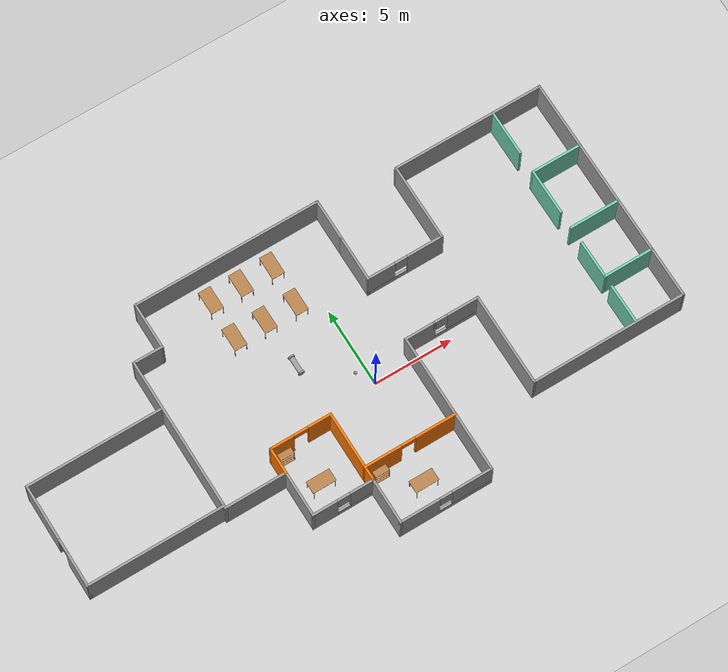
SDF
<sdf version="1.6">
 <world name="default">
  <plugin name="welcome" filename="libwelcome.so"/>
  <light name="sun" type="directional">
   <pose>0 0 10 0 -0 0</pose>
   <diffuse>0.8 0.8 0.8 1</diffuse>
   <specular>0.2 0.2 0.2 1</specular>
   <attenuation>
    <range>1000</range>
    <constant>0.9</constant>
    <linear>0.01</linear>
    <quadratic>0.001</quadratic>
   </attenuation>
   <direction>-0.5 0.1 -0.9</direction>
  </light>
  <model name="ground_plane">
   <static>1</static>
   <link name="link">
    <collision name="collision">
     <geometry><plane><normal>0 0 1</normal><size>100 100</size></plane></geometry>
     <surface>
      <contact><collide_bitmask>65535</collide_bitmask></contact>
      <friction><ode><mu>100</mu><mu2>50</mu2></ode></friction>
     </surface>
    </collision>
    <visual name="visual">
     <cast_shadows>0</cast_shadows>
     <geometry><plane><normal>0 0 1</normal><size>100 100</size></plane></geometry>
     <material>
      <script><uri>file://media/materials/scripts/gazebo.material</uri><name>Gazebo/Grey</name></script>
     </material>
    </visual>
   </link>
  </model>
  <gravity>0 0 -9.8</gravity>
  <magnetic_field>6e-06 2.3e-05 -4.2e-05</magnetic_field>
  <atmosphere type="adiabatic"/>
  <physics name="default_physics" default="0" type="ode">
   <max_step_size>0.001</max_step_size>
   <real_time_factor>1</real_time_factor>
   <real_time_update_rate>1000</real_time_update_rate>
  </physics>
  <scene><ambient>0.4 0.4 0.4 1</ambient><background>0.7 0.7 0.7 1</background><shadows>1</shadows></scene>
  <spherical_coordinates>
   <surface_model>EARTH_WGS84</surface_model>
   <latitude_deg>0</latitude_deg>
   <longitude_deg>0</longitude_deg>
   <elevation>0</elevation>
   <heading_deg>0</heading_deg>
  </spherical_coordinates>
  <model name="Project1_building">
   <pose>-1.45502 0.99671 0 0 -0 0</pose>
   <link name="Wall_35">
    <collision name="Wall_35_Collision">
     <geometry><box><size>10.0004 0.15 2.5</size></box></geometry>
     <pose>0 0 1.25 0 -0 0</pose>
    </collision>
    <visual name="Wall_35_Visual">
     <pose>0 0 1.25 0 -0 0</pose>
     <geometry><box><size>10.0004 0.15 2.5</size></box></geometry>
     <material>
      <script><uri>file://media/materials/scripts/gazebo.material</uri><name>Gazebo/Grey</name></script>
      <ambient>1 1 1 1</ambient>
     </material>
     <meta><layer>0</layer></meta>
    </visual>
    <pose>-9.74538 1.39985 0 0 0 -1.57079</pose>
   </link>
   <link name="Wall_36">
    <collision name="Wall_36_Collision">
     <geometry><box><size>4 0.15 2.5</size></box></geometry>
     <pose>0 0 1.25 0 -0 0</pose>
    </collision>
    <visual name="Wall_36_Visual">
     <pose>0 0 1.25 0 -0 0</pose>
     <geometry><box><size>4 0.15 2.5</size></box></geometry>
     <material>
      <script><uri>file://media/materials/scripts/gazebo.material</uri><name>Gazebo/Grey</name></script>
      <ambient>1 1 1 1</ambient>
     </material>
     <meta><layer>0</layer></meta>
    </visual>
    <pose>-7.82036 -3.52533 0 0 -0 0</pose>
   </link>
   <link name="Wall_37">
    <collision name="Wall_37_Collision">
     <geometry><box><size>3 0.15 2.5</size></box></geometry>
     <pose>0 0 1.25 0 -0 0</pose>
    </collision>
    <visual name="Wall_37_Visual">
     <pose>0 0 1.25 0 -0 0</pose>
     <geometry><box><size>3 0.15 2.5</size></box></geometry>
     <material>
      <script><uri>file://media/materials/scripts/gazebo.material</uri><name>Gazebo/Grey</name></script>
      <ambient>1 1 1 1</ambient>
     </material>
     <meta><layer>0</layer></meta>
    </visual>
    <pose>-5.89538 -4.95015 0 0 0 -1.57081</pose>
   </link>
   <link name="Wall_38">
    <pose>-3.97038 -6.37481 0 0 -0 8.5e-05</pose>
    <visual name="Wall_38_Visual_0">
     <pose>-1.18388 0 1.25 0 -0 0</pose>
     <geometry><box><size>1.63229 0.15 2.5</size></box></geometry>
     <material>
      <script><uri>file://media/materials/scripts/gazebo.material</uri><name>Gazebo/Grey</name></script>
      <ambient>1 1 1 1</ambient>
     </material>
     <meta><layer>0</layer></meta>
    </visual>
    <collision name="Wall_38_Collision_0">
     <geometry><box><size>1.63229 0.15 2.5</size></box></geometry>
     <pose>-1.18388 0 1.25 0 -0 0</pose>
    </collision>
    <visual name="Wall_38_Visual_1">
     <pose>0.816147 0 0.25 0 -0 0</pose>
     <geometry><box><size>2.36775 0.15 0.5</size></box></geometry>
     <material>
      <script><uri>file://media/materials/scripts/gazebo.material</uri><name>Gazebo/Grey</name></script>
      <ambient>1 1 1 1</ambient>
     </material>
     <meta><layer>0</layer></meta>
    </visual>
    <collision name="Wall_38_Collision_1">
     <geometry><box><size>2.36775 0.15 0.5</size></box></geometry>
     <pose>0.816147 0 0.25 0 -0 0</pose>
    </collision>
    <visual name="Wall_38_Visual_2">
     <pose>1.21615 0 1.5 0 -0 0</pose>
     <geometry><box><size>1.56775 0.15 2</size></box></geometry>
     <material>
      <script><uri>file://media/materials/scripts/gazebo.material</uri><name>Gazebo/Grey</name></script>
      <ambient>1 1 1 1</ambient>
     </material>
     <meta><layer>0</layer></meta>
    </visual>
    <collision name="Wall_38_Collision_2">
     <geometry><box><size>1.56775 0.15 2</size></box></geometry>
     <pose>1.21615 0 1.5 0 -0 0</pose>
    </collision>
    <visual name="Wall_38_Visual_3">
     <pose>0.032272 0 1.9 0 -0 0</pose>
     <geometry><box><size>0.8 0.15 1.2</size></box></geometry>
     <material>
      <script><uri>file://media/materials/scripts/gazebo.material</uri><name>Gazebo/Grey</name></script>
      <ambient>1 1 1 1</ambient>
     </material>
     <meta><layer>0</layer></meta>
    </visual>
    <collision name="Wall_38_Collision_3">
     <geometry><box><size>0.8 0.15 1.2</size></box></geometry>
     <pose>0.032272 0 1.9 0 -0 0</pose>
    </collision>
   </link>
   <link name="Wall_39">
    <collision name="Wall_39_Collision">
     <geometry><box><size>3.00042 0.15 2.5</size></box></geometry>
     <pose>0 0 1.25 0 -0 0</pose>
    </collision>
    <visual name="Wall_39_Visual">
     <pose>0 0 1.25 0 -0 0</pose>
     <geometry><box><size>3.00042 0.15 2.5</size></box></geometry>
     <material>
      <script><uri>file://media/materials/scripts/gazebo.material</uri><name>Gazebo/Grey</name></script>
      <ambient>1 1 1 1</ambient>
     </material>
     <meta><layer>0</layer></meta>
    </visual>
    <pose>-2.04538 -7.79981 0 0 0 -1.57081</pose>
   </link>
   <link name="Wall_40">
    <pose>0.879597 -9.22498 0 0 -0 0</pose>
    <visual name="Wall_40_Visual_0">
     <pose>-1.7008 0 1.25 0 -0 0</pose>
     <geometry><box><size>2.59839 0.15 2.5</size></box></geometry>
     <material>
      <script><uri>file://media/materials/scripts/gazebo.material</uri><name>Gazebo/Grey</name></script>
      <ambient>1 1 1 1</ambient>
     </material>
     <meta><layer>0</layer></meta>
    </visual>
    <collision name="Wall_40_Collision_0">
     <geometry><box><size>2.59839 0.15 2.5</size></box></geometry>
     <pose>-1.7008 0 1.25 0 -0 0</pose>
    </collision>
    <visual name="Wall_40_Visual_1">
     <pose>1.2992 0 0.25 0 -0 0</pose>
     <geometry><box><size>3.40161 0.15 0.5</size></box></geometry>
     <material>
      <script><uri>file://media/materials/scripts/gazebo.material</uri><name>Gazebo/Grey</name></script>
      <ambient>1 1 1 1</ambient>
     </material>
     <meta><layer>0</layer></meta>
    </visual>
    <collision name="Wall_40_Collision_1">
     <geometry><box><size>3.40161 0.15 0.5</size></box></geometry>
     <pose>1.2992 0 0.25 0 -0 0</pose>
    </collision>
    <visual name="Wall_40_Visual_2">
     <pose>1.6992 0 1.5 0 -0 0</pose>
     <geometry><box><size>2.60161 0.15 2</size></box></geometry>
     <material>
      <script><uri>file://media/materials/scripts/gazebo.material</uri><name>Gazebo/Grey</name></script>
      <ambient>1 1 1 1</ambient>
     </material>
     <meta><layer>0</layer></meta>
    </visual>
    <collision name="Wall_40_Collision_2">
     <geometry><box><size>2.60161 0.15 2</size></box></geometry>
     <pose>1.6992 0 1.5 0 -0 0</pose>
    </collision>
    <visual name="Wall_40_Visual_3">
     <pose>-0.001609 0 1.9 0 -0 0</pose>
     <geometry><box><size>0.8 0.15 1.2</size></box></geometry>
     <material>
      <script><uri>file://media/materials/scripts/gazebo.material</uri><name>Gazebo/Grey</name></script>
      <ambient>1 1 1 1</ambient>
     </material>
     <meta><layer>0</layer></meta>
    </visual>
    <collision name="Wall_40_Collision_3">
     <geometry><box><size>0.8 0.15 1.2</size></box></geometry>
     <pose>-0.001609 0 1.9 0 -0 0</pose>
    </collision>
   </link>
   <link name="Wall_41">
    <collision name="Wall_41_Collision">
     <geometry><box><size>9 0.15 2.5</size></box></geometry>
     <pose>0 0 1.25 0 -0 0</pose>
    </collision>
    <visual name="Wall_41_Visual">
     <pose>0 0 1.25 0 -0 0</pose>
     <geometry><box><size>9 0.15 2.5</size></box></geometry>
     <material>
      <script><uri>file://media/materials/scripts/gazebo.material</uri><name>Gazebo/Grey</name></script>
      <ambient>1 1 1 1</ambient>
     </material>
     <meta><layer>0</layer></meta>
    </visual>
    <pose>3.8046 -4.79998 0 0 -0 1.5708</pose>
   </link>
   <link name="Wall_42">
    <collision name="Wall_42_Collision">
     <geometry><box><size>2 0.15 2.5</size></box></geometry>
     <pose>0 0 1.25 0 -0 0</pose>
    </collision>
    <visual name="Wall_42_Visual">
     <pose>0 0 1.25 0 -0 0</pose>
     <geometry><box><size>2 0.15 2.5</size></box></geometry>
     <material>
      <script><uri>file://media/materials/scripts/gazebo.material</uri><name>Gazebo/Grey</name></script>
      <ambient>1 1 1 1</ambient>
     </material>
     <meta><layer>0</layer></meta>
    </visual>
    <pose>4.7296 -0.374976 0 0 -0 0</pose>
   </link>
   <link name="Wall_43">
    <pose>7.0796 -0.374976 0 0 -0 0</pose>
    <visual name="Wall_43_Visual_0">
     <pose>-1.44424 0 1.25 0 -0 0</pose>
     <geometry><box><size>0.111524 0.15 2.5</size></box></geometry>
     <material>
      <script><uri>file://media/materials/scripts/gazebo.material</uri><name>Gazebo/Grey</name></script>
      <ambient>1 1 1 1</ambient>
     </material>
     <meta><layer>0</layer></meta>
    </visual>
    <collision name="Wall_43_Collision_0">
     <geometry><box><size>0.111524 0.15 2.5</size></box></geometry>
     <pose>-1.44424 0 1.25 0 -0 0</pose>
    </collision>
    <visual name="Wall_43_Visual_1">
     <pose>0.055762 0 0.25 0 -0 0</pose>
     <geometry><box><size>2.88848 0.15 0.5</size></box></geometry>
     <material>
      <script><uri>file://media/materials/scripts/gazebo.material</uri><name>Gazebo/Grey</name></script>
      <ambient>1 1 1 1</ambient>
     </material>
     <meta><layer>0</layer></meta>
    </visual>
    <collision name="Wall_43_Collision_1">
     <geometry><box><size>2.88848 0.15 0.5</size></box></geometry>
     <pose>0.055762 0 0.25 0 -0 0</pose>
    </collision>
    <visual name="Wall_43_Visual_2">
     <pose>0.455762 0 1.5 0 -0 0</pose>
     <geometry><box><size>2.08848 0.15 2</size></box></geometry>
     <material>
      <script><uri>file://media/materials/scripts/gazebo.material</uri><name>Gazebo/Grey</name></script>
      <ambient>1 1 1 1</ambient>
     </material>
     <meta><layer>0</layer></meta>
    </visual>
    <collision name="Wall_43_Collision_2">
     <geometry><box><size>2.08848 0.15 2</size></box></geometry>
     <pose>0.455762 0 1.5 0 -0 0</pose>
    </collision>
    <visual name="Wall_43_Visual_3">
     <pose>-0.988476 0 1.9 0 -0 0</pose>
     <geometry><box><size>0.8 0.15 1.2</size></box></geometry>
     <material>
      <script><uri>file://media/materials/scripts/gazebo.material</uri><name>Gazebo/Grey</name></script>
      <ambient>1 1 1 1</ambient>
     </material>
     <meta><layer>0</layer></meta>
    </visual>
    <collision name="Wall_43_Collision_3">
     <geometry><box><size>0.8 0.15 1.2</size></box></geometry>
     <pose>-0.988476 0 1.9 0 -0 0</pose>
    </collision>
   </link>
   <link name="Wall_44">
    <collision name="Wall_44_Collision">
     <geometry><box><size>6 0.15 2.5</size></box></geometry>
     <pose>0 0 1.25 0 -0 0</pose>
    </collision>
    <visual name="Wall_44_Visual">
     <pose>0 0 1.25 0 -0 0</pose>
     <geometry><box><size>6 0.15 2.5</size></box></geometry>
     <material>
      <script><uri>file://media/materials/scripts/gazebo.material</uri><name>Gazebo/Grey</name></script>
      <ambient>1 1 1 1</ambient>
     </material>
     <meta><layer>0</layer></meta>
    </visual>
    <pose>8.5046 -3.29998 0 0 0 -1.5708</pose>
   </link>
   <link name="Wall_45">
    <collision name="Wall_45_Collision">
     <geometry><box><size>10 0.15 2.5</size></box></geometry>
     <pose>0 0 1.25 0 -0 0</pose>
    </collision>
    <visual name="Wall_45_Visual">
     <pose>0 0 1.25 0 -0 0</pose>
     <geometry><box><size>10 0.15 2.5</size></box></geometry>
     <material>
      <script><uri>file://media/materials/scripts/gazebo.material</uri><name>Gazebo/Grey</name></script>
      <ambient>1 1 1 1</ambient>
     </material>
     <meta><layer>0</layer></meta>
    </visual>
    <pose>13.4296 -6.22498 0 0 -0 0</pose>
   </link>
   <link name="Wall_46">
    <collision name="Wall_46_Collision">
     <geometry><box><size>15 0.15 2.5</size></box></geometry>
     <pose>0 0 1.25 0 -0 0</pose>
    </collision>
    <visual name="Wall_46_Visual">
     <pose>0 0 1.25 0 -0 0</pose>
     <geometry><box><size>15 0.15 2.5</size></box></geometry>
     <material>
      <script><uri>file://media/materials/scripts/gazebo.material</uri><name>Gazebo/Grey</name></script>
      <ambient>1 1 1 1</ambient>
     </material>
     <meta><layer>0</layer></meta>
    </visual>
    <pose>18.3546 1.20002 0 0 -0 1.5708</pose>
   </link>
   <link name="Wall_47">
    <collision name="Wall_47_Collision">
     <geometry><box><size>9.75 0.15 2.5</size></box></geometry>
     <pose>0 0 1.25 0 -0 0</pose>
    </collision>
    <visual name="Wall_47_Visual">
     <pose>0 0 1.25 0 -0 0</pose>
     <geometry><box><size>9.75 0.15 2.5</size></box></geometry>
     <material>
      <script><uri>file://media/materials/scripts/gazebo.material</uri><name>Gazebo/Grey</name></script>
      <ambient>1 1 1 1</ambient>
     </material>
     <meta><layer>0</layer></meta>
    </visual>
    <pose>13.5546 8.62502 0 0 -0 3.14159</pose>
   </link>
   <link name="Wall_48">
    <collision name="Wall_48_Collision">
     <geometry><box><size>5 0.15 2.5</size></box></geometry>
     <pose>0 0 1.25 0 -0 0</pose>
    </collision>
    <visual name="Wall_48_Visual">
     <pose>0 0 1.25 0 -0 0</pose>
     <geometry><box><size>5 0.15 2.5</size></box></geometry>
     <material>
      <script><uri>file://media/materials/scripts/gazebo.material</uri><name>Gazebo/Grey</name></script>
      <ambient>1 1 1 1</ambient>
     </material>
     <meta><layer>0</layer></meta>
    </visual>
    <pose>8.7546 6.20003 0 0 0 -1.5708</pose>
   </link>
   <link name="Wall_49">
    <pose>6.3296 3.77502 0 0 -0 3.14159</pose>
    <visual name="Wall_49_Visual_0">
     <pose>-1.31529 0 1.25 0 -0 0</pose>
     <geometry><box><size>2.36941 0.15 2.5</size></box></geometry>
     <material>
      <script><uri>file://media/materials/scripts/gazebo.material</uri><name>Gazebo/Grey</name></script>
      <ambient>1 1 1 1</ambient>
     </material>
     <meta><layer>0</layer></meta>
    </visual>
    <collision name="Wall_49_Collision_0">
     <geometry><box><size>2.36941 0.15 2.5</size></box></geometry>
     <pose>-1.31529 0 1.25 0 -0 0</pose>
    </collision>
    <visual name="Wall_49_Visual_1">
     <pose>1.18471 0 0.25 0 -0 0</pose>
     <geometry><box><size>2.63059 0.15 0.5</size></box></geometry>
     <material>
      <script><uri>file://media/materials/scripts/gazebo.material</uri><name>Gazebo/Grey</name></script>
      <ambient>1 1 1 1</ambient>
     </material>
     <meta><layer>0</layer></meta>
    </visual>
    <collision name="Wall_49_Collision_1">
     <geometry><box><size>2.63059 0.15 0.5</size></box></geometry>
     <pose>1.18471 0 0.25 0 -0 0</pose>
    </collision>
    <visual name="Wall_49_Visual_2">
     <pose>1.58471 0 1.5 0 -0 0</pose>
     <geometry><box><size>1.83059 0.15 2</size></box></geometry>
     <material>
      <script><uri>file://media/materials/scripts/gazebo.material</uri><name>Gazebo/Grey</name></script>
      <ambient>1 1 1 1</ambient>
     </material>
     <meta><layer>0</layer></meta>
    </visual>
    <collision name="Wall_49_Collision_2">
     <geometry><box><size>1.83059 0.15 2</size></box></geometry>
     <pose>1.58471 0 1.5 0 -0 0</pose>
    </collision>
    <visual name="Wall_49_Visual_3">
     <pose>0.269414 0 1.9 0 -0 0</pose>
     <geometry><box><size>0.8 0.15 1.2</size></box></geometry>
     <material>
      <script><uri>file://media/materials/scripts/gazebo.material</uri><name>Gazebo/Grey</name></script>
      <ambient>1 1 1 1</ambient>
     </material>
     <meta><layer>0</layer></meta>
    </visual>
    <collision name="Wall_49_Collision_3">
     <geometry><box><size>0.8 0.15 1.2</size></box></geometry>
     <pose>0.269414 0 1.9 0 -0 0</pose>
    </collision>
   </link>
   <link name="Wall_50">
    <collision name="Wall_50_Collision">
     <geometry><box><size>3 0.15 2.5</size></box></geometry>
     <pose>0 0 1.25 0 -0 0</pose>
    </collision>
    <visual name="Wall_50_Visual">
     <pose>0 0 1.25 0 -0 0</pose>
     <geometry><box><size>3 0.15 2.5</size></box></geometry>
     <material>
      <script><uri>file://media/materials/scripts/gazebo.material</uri><name>Gazebo/Grey</name></script>
      <ambient>1 1 1 1</ambient>
     </material>
     <meta><layer>0</layer></meta>
    </visual>
    <pose>3.9046 5.20003 0 0 -0 1.5708</pose>
   </link>
   <link name="Wall_51">
    <collision name="Wall_51_Collision">
     <geometry><box><size>2.75 0.15 2.5</size></box></geometry>
     <pose>0 0 1.25 0 -0 0</pose>
    </collision>
    <visual name="Wall_51_Visual">
     <pose>0 0 1.25 0 -0 0</pose>
     <geometry><box><size>2.75 0.15 2.5</size></box></geometry>
     <material>
      <script><uri>file://media/materials/scripts/gazebo.material</uri><name>Gazebo/Grey</name></script>
      <ambient>1 1 1 1</ambient>
     </material>
     <meta><layer>0</layer></meta>
    </visual>
    <pose>3.9046 7.92502 0 0 -0 1.5708</pose>
   </link>
   <link name="Wall_52">
    <collision name="Wall_52_Collision">
     <geometry><box><size>12 0.15 2.5</size></box></geometry>
     <pose>0 0 1.25 0 -0 0</pose>
    </collision>
    <visual name="Wall_52_Visual">
     <pose>0 0 1.25 0 -0 0</pose>
     <geometry><box><size>12 0.15 2.5</size></box></geometry>
     <material>
      <script><uri>file://media/materials/scripts/gazebo.material</uri><name>Gazebo/Grey</name></script>
      <ambient>1 1 1 1</ambient>
     </material>
     <meta><layer>0</layer></meta>
    </visual>
    <pose>-2.02038 9.22485 0 0 0 -3.14156</pose>
   </link>
   <link name="Wall_53">
    <collision name="Wall_53_Collision">
     <geometry><box><size>3.05 0.15 2.5</size></box></geometry>
     <pose>0 0 1.25 0 -0 0</pose>
    </collision>
    <visual name="Wall_53_Visual">
     <pose>0 0 1.25 0 -0 0</pose>
     <geometry><box><size>3.05 0.15 2.5</size></box></geometry>
     <material>
      <script><uri>file://media/materials/scripts/gazebo.material</uri><name>Gazebo/Grey</name></script>
      <ambient>1 1 1 1</ambient>
     </material>
     <meta><layer>0</layer></meta>
    </visual>
    <pose>-7.94536 7.77467 0 0 0 -1.5708</pose>
   </link>
   <link name="Wall_54">
    <collision name="Wall_54_Collision">
     <geometry><box><size>1.95069 0.15 2.5</size></box></geometry>
     <pose>0 0 1.25 0 -0 0</pose>
    </collision>
    <visual name="Wall_54_Visual">
     <pose>0 0 1.25 0 -0 0</pose>
     <geometry><box><size>1.95069 0.15 2.5</size></box></geometry>
     <material>
      <script><uri>file://media/materials/scripts/gazebo.material</uri><name>Gazebo/Grey</name></script>
      <ambient>1 1 1 1</ambient>
     </material>
     <meta><layer>0</layer></meta>
    </visual>
    <pose>-8.84538 6.32485 0 0 -0 3.1414</pose>
   </link>
   <link name="Wall_56">
    <collision name="Wall_56_Collision">
     <geometry><box><size>1 0.15 2.5</size></box></geometry>
     <pose>0 0 1.25 0 -0 0</pose>
    </collision>
    <visual name="Wall_56_Visual">
     <pose>0 0 1.25 0 -0 0</pose>
     <geometry><box><size>1 0.15 2.5</size></box></geometry>
     <material>
      <script><uri>file://media/materials/scripts/gazebo.material</uri><name>Gazebo/Grey</name></script>
      <ambient>0.996078 0.47451 0.0196078 1</ambient>
     </material>
     <meta><layer>0</layer></meta>
    </visual>
    <pose>-2.03353 -5.94949 0 0 -0 1.59861</pose>
   </link>
   <link name="Wall_57">
    <pose>0.879641 -5.52483 0 0 0 -0.000171</pose>
    <visual name="Wall_57_Visual_0">
     <pose>-1.78854 0 1.25 0 -0 0</pose>
     <geometry><box><size>2.42292 0.15 2.5</size></box></geometry>
     <material>
      <script><uri>file://media/materials/scripts/gazebo.material</uri><name>Gazebo/Grey</name></script>
      <ambient>0.996078 0.47451 0.0196078 1</ambient>
     </material>
     <meta><layer>0</layer></meta>
    </visual>
    <collision name="Wall_57_Collision_0">
     <geometry><box><size>2.42292 0.15 2.5</size></box></geometry>
     <pose>-1.78854 0 1.25 0 -0 0</pose>
    </collision>
    <visual name="Wall_57_Visual_1">
     <pose>1.66146 0 1.25 0 -0 0</pose>
     <geometry><box><size>2.67708 0.15 2.5</size></box></geometry>
     <material>
      <script><uri>file://media/materials/scripts/gazebo.material</uri><name>Gazebo/Grey</name></script>
      <ambient>0.996078 0.47451 0.0196078 1</ambient>
     </material>
     <meta><layer>0</layer></meta>
    </visual>
    <collision name="Wall_57_Collision_1">
     <geometry><box><size>2.67708 0.15 2.5</size></box></geometry>
     <pose>1.66146 0 1.25 0 -0 0</pose>
    </collision>
    <visual name="Wall_57_Visual_2">
     <pose>-0.127078 0 2.25 0 -0 0</pose>
     <geometry><box><size>0.9 0.15 0.5</size></box></geometry>
     <material>
      <script><uri>file://media/materials/scripts/gazebo.material</uri><name>Gazebo/Grey</name></script>
      <ambient>0.996078 0.47451 0.0196078 1</ambient>
     </material>
     <meta><layer>0</layer></meta>
    </visual>
    <collision name="Wall_57_Collision_2">
     <geometry><box><size>0.9 0.15 0.5</size></box></geometry>
     <pose>-0.127078 0 2.25 0 -0 0</pose>
    </collision>
   </link>
   <link name="Wall_59">
    <collision name="Wall_59_Collision">
     <geometry><box><size>1.75 0.15 2.5</size></box></geometry>
     <pose>0 0 1.25 0 -0 0</pose>
    </collision>
    <visual name="Wall_59_Visual">
     <pose>0 0 1.25 0 -0 0</pose>
     <geometry><box><size>1.75 0.15 2.5</size></box></geometry>
     <material>
      <script><uri>file://media/materials/scripts/gazebo.material</uri><name>Gazebo/Grey</name></script>
      <ambient>0.996078 0.47451 0.0196078 1</ambient>
     </material>
     <meta><layer>0</layer></meta>
    </visual>
    <pose>-5.89536 -2.72533 0 0 -0 1.5708</pose>
   </link>
   <link name="Wall_62">
    <collision name="Wall_62_Collision">
     <geometry><box><size>3.74975 0.15 2.5</size></box></geometry>
     <pose>0 0 1.25 0 -0 0</pose>
    </collision>
    <visual name="Wall_62_Visual">
     <pose>0 0 1.25 0 -0 0</pose>
     <geometry><box><size>3.74975 0.15 2.5</size></box></geometry>
     <material>
      <script><uri>file://media/materials/scripts/gazebo.material</uri><name>Gazebo/Grey</name></script>
      <ambient>0.996078 0.47451 0.0196078 1</ambient>
     </material>
     <meta><layer>0</layer></meta>
    </visual>
    <pose>-2.04536 -3.72483 0 0 -0 1.5708</pose>
   </link>
   <link name="Wall_63">
    <pose>-3.97036 -1.92533 0 0 -0 3.14159</pose>
    <visual name="Wall_63_Visual_0">
     <pose>-1.22397 0 1.25 0 -0 0</pose>
     <geometry><box><size>1.55205 0.15 2.5</size></box></geometry>
     <material>
      <script><uri>file://media/materials/scripts/gazebo.material</uri><name>Gazebo/Grey</name></script>
      <ambient>0.996078 0.47451 0.0196078 1</ambient>
     </material>
     <meta><layer>0</layer></meta>
    </visual>
    <collision name="Wall_63_Collision_0">
     <geometry><box><size>1.55205 0.15 2.5</size></box></geometry>
     <pose>-1.22397 0 1.25 0 -0 0</pose>
    </collision>
    <visual name="Wall_63_Visual_1">
     <pose>1.22603 0 1.25 0 -0 0</pose>
     <geometry><box><size>1.54795 0.15 2.5</size></box></geometry>
     <material>
      <script><uri>file://media/materials/scripts/gazebo.material</uri><name>Gazebo/Grey</name></script>
      <ambient>0.996078 0.47451 0.0196078 1</ambient>
     </material>
     <meta><layer>0</layer></meta>
    </visual>
    <collision name="Wall_63_Collision_1">
     <geometry><box><size>1.54795 0.15 2.5</size></box></geometry>
     <pose>1.22603 0 1.25 0 -0 0</pose>
    </collision>
    <visual name="Wall_63_Visual_2">
     <pose>0.002054 0 2.25 0 -0 0</pose>
     <geometry><box><size>0.9 0.15 0.5</size></box></geometry>
     <material>
      <script><uri>file://media/materials/scripts/gazebo.material</uri><name>Gazebo/Grey</name></script>
      <ambient>0.996078 0.47451 0.0196078 1</ambient>
     </material>
     <meta><layer>0</layer></meta>
    </visual>
    <collision name="Wall_63_Collision_2">
     <geometry><box><size>0.9 0.15 0.5</size></box></geometry>
     <pose>0.002054 0 2.25 0 -0 0</pose>
    </collision>
   </link>
   <link name="Wall_65">
    <collision name="Wall_65_Collision">
     <geometry><box><size>8.61907 0.15 2.5</size></box></geometry>
     <pose>0 0 1.25 0 -0 0</pose>
    </collision>
    <visual name="Wall_65_Visual">
     <pose>0 0 1.25 0 -0 0</pose>
     <geometry><box><size>8.61907 0.15 2.5</size></box></geometry>
     <material>
      <script><uri>file://media/materials/scripts/gazebo.material</uri><name>Gazebo/Grey</name></script>
      <ambient>1 1 1 1</ambient>
     </material>
     <meta><layer>0</layer></meta>
    </visual>
    <pose>-14.1201 3.22011 0 0 -0 3.14159</pose>
   </link>
   <link name="Wall_73">
    <pose>-18.3546 -0.079888 0 0 0 -1.5708</pose>
    <visual name="Wall_73_Visual_0">
     <pose>-1.57968 0 1.25 0 -0 0</pose>
     <geometry><box><size>3.59064 0.15 2.5</size></box></geometry>
     <material>
      <script><uri>file://media/materials/scripts/gazebo.material</uri><name>Gazebo/Grey</name></script>
      <ambient>1 1 1 1</ambient>
     </material>
     <meta><layer>0</layer></meta>
    </visual>
    <collision name="Wall_73_Collision_0">
     <geometry><box><size>3.59064 0.15 2.5</size></box></geometry>
     <pose>-1.57968 0 1.25 0 -0 0</pose>
    </collision>
    <visual name="Wall_73_Visual_1">
     <pose>2.24532 0 1.25 0 -0 0</pose>
     <geometry><box><size>2.25936 0.15 2.5</size></box></geometry>
     <material>
      <script><uri>file://media/materials/scripts/gazebo.material</uri><name>Gazebo/Grey</name></script>
      <ambient>1 1 1 1</ambient>
     </material>
     <meta><layer>0</layer></meta>
    </visual>
    <collision name="Wall_73_Collision_1">
     <geometry><box><size>2.25936 0.15 2.5</size></box></geometry>
     <pose>2.24532 0 1.25 0 -0 0</pose>
    </collision>
    <visual name="Wall_73_Visual_2">
     <pose>0.665644 0 2.25 0 -0 0</pose>
     <geometry><box><size>0.9 0.15 0.5</size></box></geometry>
     <material>
      <script><uri>file://media/materials/scripts/gazebo.material</uri><name>Gazebo/Grey</name></script>
      <ambient>1 1 1 1</ambient>
     </material>
     <meta><layer>0</layer></meta>
    </visual>
    <collision name="Wall_73_Collision_2">
     <geometry><box><size>0.9 0.15 0.5</size></box></geometry>
     <pose>0.665644 0 2.25 0 -0 0</pose>
    </collision>
   </link>
   <link name="Wall_74">
    <collision name="Wall_74_Collision">
     <geometry><box><size>8.75 0.15 2.5</size></box></geometry>
     <pose>0 0 1.25 0 -0 0</pose>
    </collision>
    <visual name="Wall_74_Visual">
     <pose>0 0 1.25 0 -0 0</pose>
     <geometry><box><size>8.75 0.15 2.5</size></box></geometry>
     <material>
      <script><uri>file://media/materials/scripts/gazebo.material</uri><name>Gazebo/Grey</name></script>
      <ambient>1 1 1 1</ambient>
     </material>
     <meta><layer>0</layer></meta>
    </visual>
    <pose>-14.0546 -3.37989 0 0 -0 0</pose>
   </link>
   <link name="Wall_76">
    <collision name="Wall_76_Collision">
     <geometry><box><size>3 0.15 2.5</size></box></geometry>
     <pose>0 0 1.25 0 -0 0</pose>
    </collision>
    <visual name="Wall_76_Visual">
     <pose>0 0 1.25 0 -0 0</pose>
     <geometry><box><size>3 0.15 2.5</size></box></geometry>
     <material>
      <script><uri>file://media/materials/scripts/gazebo.material</uri><name>Gazebo/Grey</name></script>
      <ambient>0.435294 0.796078 0.67451 1</ambient>
     </material>
     <meta><layer>0</layer></meta>
    </visual>
    <pose>15.2266 7.19767 0 0 0 -1.5708</pose>
   </link>
   <link name="Wall_81">
    <collision name="Wall_81_Collision">
     <geometry><box><size>3 0.15 2.5</size></box></geometry>
     <pose>0 0 1.25 0 -0 0</pose>
    </collision>
    <visual name="Wall_81_Visual">
     <pose>0 0 1.25 0 -0 0</pose>
     <geometry><box><size>3 0.15 2.5</size></box></geometry>
     <material>
      <script><uri>file://media/materials/scripts/gazebo.material</uri><name>Gazebo/Grey</name></script>
      <ambient>0.435294 0.796078 0.67451 1</ambient>
     </material>
     <meta><layer>0</layer></meta>
    </visual>
    <pose>15.2266 2.95067 0 0 0 -1.5708</pose>
   </link>
   <link name="Wall_87">
    <collision name="Wall_87_Collision">
     <geometry><box><size>3.25 0.15 2.5</size></box></geometry>
     <pose>0 0 1.25 0 -0 0</pose>
    </collision>
    <visual name="Wall_87_Visual">
     <pose>0 0 1.25 0 -0 0</pose>
     <geometry><box><size>3.25 0.15 2.5</size></box></geometry>
     <material>
      <script><uri>file://media/materials/scripts/gazebo.material</uri><name>Gazebo/Grey</name></script>
      <ambient>0.435294 0.796078 0.67451 1</ambient>
     </material>
     <meta><layer>0</layer></meta>
    </visual>
    <pose>16.7766 4.37567 0 0 -0 0</pose>
   </link>
   <link name="Wall_89">
    <collision name="Wall_89_Collision">
     <geometry><box><size>3.26808 0.15 2.5</size></box></geometry>
     <pose>0 0 1.25 0 -0 0</pose>
    </collision>
    <visual name="Wall_89_Visual">
     <pose>0 0 1.25 0 -0 0</pose>
     <geometry><box><size>3.26808 0.15 2.5</size></box></geometry>
     <material>
      <script><uri>file://media/materials/scripts/gazebo.material</uri><name>Gazebo/Grey</name></script>
      <ambient>0.435294 0.796078 0.67451 1</ambient>
     </material>
     <meta><layer>0</layer></meta>
    </visual>
    <pose>16.7856 0.405672 0 0 -0 0</pose>
   </link>
   <link name="Wall_94">
    <collision name="Wall_94_Collision">
     <geometry><box><size>3.25 0.15 2.5</size></box></geometry>
     <pose>0 0 1.25 0 -0 0</pose>
    </collision>
    <visual name="Wall_94_Visual">
     <pose>0 0 1.25 0 -0 0</pose>
     <geometry><box><size>3.25 0.15 2.5</size></box></geometry>
     <material>
      <script><uri>file://media/materials/scripts/gazebo.material</uri><name>Gazebo/Grey</name></script>
      <ambient>0.435294 0.796078 0.67451 1</ambient>
     </material>
     <meta><layer>0</layer></meta>
    </visual>
    <pose>16.7766 -3.04433 0 0 -0 0</pose>
   </link>
   <link name="Wall_96">
    <collision name="Wall_96_Collision">
     <geometry><box><size>2.5 0.15 2.5</size></box></geometry>
     <pose>0 0 1.25 0 -0 0</pose>
    </collision>
    <visual name="Wall_96_Visual">
     <pose>0 0 1.25 0 -0 0</pose>
     <geometry><box><size>2.5 0.15 2.5</size></box></geometry>
     <material>
      <script><uri>file://media/materials/scripts/gazebo.material</uri><name>Gazebo/Grey</name></script>
      <ambient>0.435294 0.796078 0.67451 1</ambient>
     </material>
     <meta><layer>0</layer></meta>
    </visual>
    <pose>15.2266 -1.87233 0 0 0 -1.5708</pose>
   </link>
   <link name="Wall_98">
    <collision name="Wall_98_Collision">
     <geometry><box><size>2.5 0.15 2.5</size></box></geometry>
     <pose>0 0 1.25 0 -0 0</pose>
    </collision>
    <visual name="Wall_98_Visual">
     <pose>0 0 1.25 0 -0 0</pose>
     <geometry><box><size>2.5 0.15 2.5</size></box></geometry>
     <material>
      <script><uri>file://media/materials/scripts/gazebo.material</uri><name>Gazebo/Grey</name></script>
      <ambient>0.435294 0.796078 0.67451 1</ambient>
     </material>
     <meta><layer>0</layer></meta>
    </visual>
    <pose>15.2266 -4.93933 0 0 0 -1.5708</pose>
   </link>
   <static>1</static>
  </model>
  <model name="bookshelf">
   <static>1</static>
   <link name="link">
    <inertial><mass>1</mass></inertial>
    <collision name="back">
     <pose>0 0.005 0.6 0 -0 0</pose>
     <geometry><box><size>0.9 0.01 1.2</size></box></geometry>
    </collision>
    <visual name="visual1">
     <pose>0 0.005 0.6 0 -0 0</pose>
     <geometry><box><size>0.9 0.01 1.2</size></box></geometry>
     <material>
      <script><uri>file://media/materials/scripts/gazebo.material</uri><name>Gazebo/Wood</name></script>
     </material>
    </visual>
    <collision name="left_side">
     <pose>0.45 -0.195 0.6 0 -0 0</pose>
     <geometry><box><size>0.02 0.4 1.2</size></box></geometry>
    </collision>
    <visual name="visual2">
     <pose>0.45 -0.195 0.6 0 -0 0</pose>
     <geometry><box><size>0.02 0.4 1.2</size></box></geometry>
     <material>
      <script><uri>file://media/materials/scripts/gazebo.material</uri><name>Gazebo/Wood</name></script>
     </material>
    </visual>
    <collision name="right_side">
     <pose>-0.45 -0.195 0.6 0 -0 0</pose>
     <geometry><box><size>0.02 0.4 1.2</size></box></geometry>
    </collision>
    <visual name="visual3">
     <pose>-0.45 -0.195 0.6 0 -0 0</pose>
     <geometry><box><size>0.02 0.4 1.2</size></box></geometry>
     <material>
      <script><uri>file://media/materials/scripts/gazebo.material</uri><name>Gazebo/Wood</name></script>
     </material>
    </visual>
    <collision name="bottom">
     <pose>0 -0.195 0.03 0 -0 0</pose>
     <geometry><box><size>0.88 0.4 0.06</size></box></geometry>
    </collision>
    <visual name="visual4">
     <pose>0 -0.195 0.03 0 -0 0</pose>
     <geometry><box><size>0.88 0.4 0.06</size></box></geometry>
     <material>
      <script><uri>file://media/materials/scripts/gazebo.material</uri><name>Gazebo/Wood</name></script>
     </material>
    </visual>
    <collision name="top">
     <pose>0 -0.195 1.19 0 -0 0</pose>
     <geometry><box><size>0.88 0.4 0.02</size></box></geometry>
    </collision>
    <visual name="visual5">
     <pose>0 -0.195 1.19 0 -0 0</pose>
     <geometry><box><size>0.88 0.4 0.02</size></box></geometry>
     <material>
      <script><uri>file://media/materials/scripts/gazebo.material</uri><name>Gazebo/Wood</name></script>
     </material>
    </visual>
    <collision name="low_shelf">
     <pose>0 -0.195 0.43 0 -0 0</pose>
     <geometry><box><size>0.88 0.4 0.02</size></box></geometry>
    </collision>
    <visual name="visual6">
     <pose>0 -0.195 0.43 0 -0 0</pose>
     <geometry><box><size>0.88 0.4 0.02</size></box></geometry>
     <material>
      <script><uri>file://media/materials/scripts/gazebo.material</uri><name>Gazebo/Wood</name></script>
     </material>
    </visual>
    <collision name="high_shelf">
     <pose>0 -0.195 0.8 0 -0 0</pose>
     <geometry><box><size>0.88 0.4 0.02</size></box></geometry>
    </collision>
    <visual name="visual7">
     <pose>0 -0.195 0.8 0 -0 0</pose>
     <geometry><box><size>0.88 0.4 0.02</size></box></geometry>
     <material>
      <script><uri>file://media/materials/scripts/gazebo.material</uri><name>Gazebo/Wood</name></script>
     </material>
    </visual>
   </link>
   <pose>-2.65686 -4.63627 0 0 -0 0</pose>
  </model>
  <model name="bookshelf_0">
   <static>1</static>
   <link name="link">
    <inertial><mass>1</mass></inertial>
    <collision name="back">
     <pose>0 0.005 0.6 0 -0 0</pose>
     <geometry><box><size>0.9 0.01 1.2</size></box></geometry>
    </collision>
    <visual name="visual1">
     <pose>0 0.005 0.6 0 -0 0</pose>
     <geometry><box><size>0.9 0.01 1.2</size></box></geometry>
     <material>
      <script><uri>file://media/materials/scripts/gazebo.material</uri><name>Gazebo/Wood</name></script>
     </material>
    </visual>
    <collision name="left_side">
     <pose>0.45 -0.195 0.6 0 -0 0</pose>
     <geometry><box><size>0.02 0.4 1.2</size></box></geometry>
    </collision>
    <visual name="visual2">
     <pose>0.45 -0.195 0.6 0 -0 0</pose>
     <geometry><box><size>0.02 0.4 1.2</size></box></geometry>
     <material>
      <script><uri>file://media/materials/scripts/gazebo.material</uri><name>Gazebo/Wood</name></script>
     </material>
    </visual>
    <collision name="right_side">
     <pose>-0.45 -0.195 0.6 0 -0 0</pose>
     <geometry><box><size>0.02 0.4 1.2</size></box></geometry>
    </collision>
    <visual name="visual3">
     <pose>-0.45 -0.195 0.6 0 -0 0</pose>
     <geometry><box><size>0.02 0.4 1.2</size></box></geometry>
     <material>
      <script><uri>file://media/materials/scripts/gazebo.material</uri><name>Gazebo/Wood</name></script>
     </material>
    </visual>
    <collision name="bottom">
     <pose>0 -0.195 0.03 0 -0 0</pose>
     <geometry><box><size>0.88 0.4 0.06</size></box></geometry>
    </collision>
    <visual name="visual4">
     <pose>0 -0.195 0.03 0 -0 0</pose>
     <geometry><box><size>0.88 0.4 0.06</size></box></geometry>
     <material>
      <script><uri>file://media/materials/scripts/gazebo.material</uri><name>Gazebo/Wood</name></script>
     </material>
    </visual>
    <collision name="top">
     <pose>0 -0.195 1.19 0 -0 0</pose>
     <geometry><box><size>0.88 0.4 0.02</size></box></geometry>
    </collision>
    <visual name="visual5">
     <pose>0 -0.195 1.19 0 -0 0</pose>
     <geometry><box><size>0.88 0.4 0.02</size></box></geometry>
     <material>
      <script><uri>file://media/materials/scripts/gazebo.material</uri><name>Gazebo/Wood</name></script>
     </material>
    </visual>
    <collision name="low_shelf">
     <pose>0 -0.195 0.43 0 -0 0</pose>
     <geometry><box><size>0.88 0.4 0.02</size></box></geometry>
    </collision>
    <visual name="visual6">
     <pose>0 -0.195 0.43 0 -0 0</pose>
     <geometry><box><size>0.88 0.4 0.02</size></box></geometry>
     <material>
      <script><uri>file://media/materials/scripts/gazebo.material</uri><name>Gazebo/Wood</name></script>
     </material>
    </visual>
    <collision name="high_shelf">
     <pose>0 -0.195 0.8 0 -0 0</pose>
     <geometry><box><size>0.88 0.4 0.02</size></box></geometry>
    </collision>
    <visual name="visual7">
     <pose>0 -0.195 0.8 0 -0 0</pose>
     <geometry><box><size>0.88 0.4 0.02</size></box></geometry>
     <material>
      <script><uri>file://media/materials/scripts/gazebo.material</uri><name>Gazebo/Wood</name></script>
     </material>
    </visual>
   </link>
   <pose>-6.60588 -1.04816 0 0 -0 0</pose>
  </model>
  <model name="table_0">
   <static>1</static>
   <link name="link">
    <collision name="surface">
     <pose>0 0 1 0 -0 0</pose>
     <geometry><box><size>1.5 0.8 0.03</size></box></geometry>
     <surface><friction><ode><mu>0.6</mu><mu2>0.6</mu2></ode></friction></surface>
    </collision>
    <visual name="visual1">
     <pose>0 0 1 0 -0 0</pose>
     <geometry><box><size>1.5 0.8 0.03</size></box></geometry>
     <material>
      <script><uri>file://media/materials/scripts/gazebo.material</uri><name>Gazebo/Wood</name></script>
     </material>
    </visual>
    <collision name="front_left_leg">
     <pose>0.68 0.38 0.5 0 -0 0</pose>
     <geometry><cylinder><radius>0.02</radius><length>1</length></cylinder></geometry>
    </collision>
    <visual name="front_left_leg">
     <pose>0.68 0.38 0.5 0 -0 0</pose>
     <geometry><cylinder><radius>0.02</radius><length>1</length></cylinder></geometry>
     <material>
      <script><uri>file://media/materials/scripts/gazebo.material</uri><name>Gazebo/Grey</name></script>
     </material>
    </visual>
    <collision name="front_right_leg">
     <pose>0.68 -0.38 0.5 0 -0 0</pose>
     <geometry><cylinder><radius>0.02</radius><length>1</length></cylinder></geometry>
    </collision>
    <visual name="front_right_leg">
     <pose>0.68 -0.38 0.5 0 -0 0</pose>
     <geometry><cylinder><radius>0.02</radius><length>1</length></cylinder></geometry>
     <material>
      <script><uri>file://media/materials/scripts/gazebo.material</uri><name>Gazebo/Grey</name></script>
     </material>
    </visual>
    <collision name="back_right_leg">
     <pose>-0.68 -0.38 0.5 0 -0 0</pose>
     <geometry><cylinder><radius>0.02</radius><length>1</length></cylinder></geometry>
    </collision>
    <visual name="back_right_leg">
     <pose>-0.68 -0.38 0.5 0 -0 0</pose>
     <geometry><cylinder><radius>0.02</radius><length>1</length></cylinder></geometry>
     <material>
      <script><uri>file://media/materials/scripts/gazebo.material</uri><name>Gazebo/Grey</name></script>
     </material>
    </visual>
    <collision name="back_left_leg">
     <pose>-0.68 0.38 0.5 0 -0 0</pose>
     <geometry><cylinder><radius>0.02</radius><length>1</length></cylinder></geometry>
    </collision>
    <visual name="back_left_leg">
     <pose>-0.68 0.38 0.5 0 -0 0</pose>
     <geometry><cylinder><radius>0.02</radius><length>1</length></cylinder></geometry>
     <material>
      <script><uri>file://media/materials/scripts/gazebo.material</uri><name>Gazebo/Grey</name></script>
     </material>
    </visual>
   </link>
   <pose>-1.45 6.2 0 0 0 -1.57144</pose>
  </model>
  <model name="table_1">
   <static>1</static>
   <link name="link">
    <collision name="surface">
     <pose>0 0 1 0 -0 0</pose>
     <geometry><box><size>1.5 0.8 0.03</size></box></geometry>
     <surface><friction><ode><mu>0.6</mu><mu2>0.6</mu2></ode></friction></surface>
    </collision>
    <visual name="visual1">
     <pose>0 0 1 0 -0 0</pose>
     <geometry><box><size>1.5 0.8 0.03</size></box></geometry>
     <material>
      <script><uri>file://media/materials/scripts/gazebo.material</uri><name>Gazebo/Wood</name></script>
     </material>
    </visual>
    <collision name="front_left_leg">
     <pose>0.68 0.38 0.5 0 -0 0</pose>
     <geometry><cylinder><radius>0.02</radius><length>1</length></cylinder></geometry>
    </collision>
    <visual name="front_left_leg">
     <pose>0.68 0.38 0.5 0 -0 0</pose>
     <geometry><cylinder><radius>0.02</radius><length>1</length></cylinder></geometry>
     <material>
      <script><uri>file://media/materials/scripts/gazebo.material</uri><name>Gazebo/Grey</name></script>
     </material>
    </visual>
    <collision name="front_right_leg">
     <pose>0.68 -0.38 0.5 0 -0 0</pose>
     <geometry><cylinder><radius>0.02</radius><length>1</length></cylinder></geometry>
    </collision>
    <visual name="front_right_leg">
     <pose>0.68 -0.38 0.5 0 -0 0</pose>
     <geometry><cylinder><radius>0.02</radius><length>1</length></cylinder></geometry>
     <material>
      <script><uri>file://media/materials/scripts/gazebo.material</uri><name>Gazebo/Grey</name></script>
     </material>
    </visual>
    <collision name="back_right_leg">
     <pose>-0.68 -0.38 0.5 0 -0 0</pose>
     <geometry><cylinder><radius>0.02</radius><length>1</length></cylinder></geometry>
    </collision>
    <visual name="back_right_leg">
     <pose>-0.68 -0.38 0.5 0 -0 0</pose>
     <geometry><cylinder><radius>0.02</radius><length>1</length></cylinder></geometry>
     <material>
      <script><uri>file://media/materials/scripts/gazebo.material</uri><name>Gazebo/Grey</name></script>
     </material>
    </visual>
    <collision name="back_left_leg">
     <pose>-0.68 0.38 0.5 0 -0 0</pose>
     <geometry><cylinder><radius>0.02</radius><length>1</length></cylinder></geometry>
    </collision>
    <visual name="back_left_leg">
     <pose>-0.68 0.38 0.5 0 -0 0</pose>
     <geometry><cylinder><radius>0.02</radius><length>1</length></cylinder></geometry>
     <material>
      <script><uri>file://media/materials/scripts/gazebo.material</uri><name>Gazebo/Grey</name></script>
     </material>
    </visual>
   </link>
   <pose>-3.48 6.2 0 0.002905 -2.8e-05 -1.56136</pose>
  </model>
  <model name="table_2">
   <static>1</static>
   <link name="link">
    <collision name="surface">
     <pose>0 0 1 0 -0 0</pose>
     <geometry><box><size>1.5 0.8 0.03</size></box></geometry>
     <surface><friction><ode><mu>0.6</mu><mu2>0.6</mu2></ode></friction></surface>
    </collision>
    <visual name="visual1">
     <pose>0 0 1 0 -0 0</pose>
     <geometry><box><size>1.5 0.8 0.03</size></box></geometry>
     <material>
      <script><uri>file://media/materials/scripts/gazebo.material</uri><name>Gazebo/Wood</name></script>
     </material>
    </visual>
    <collision name="front_left_leg">
     <pose>0.68 0.38 0.5 0 -0 0</pose>
     <geometry><cylinder><radius>0.02</radius><length>1</length></cylinder></geometry>
    </collision>
    <visual name="front_left_leg">
     <pose>0.68 0.38 0.5 0 -0 0</pose>
     <geometry><cylinder><radius>0.02</radius><length>1</length></cylinder></geometry>
     <material>
      <script><uri>file://media/materials/scripts/gazebo.material</uri><name>Gazebo/Grey</name></script>
     </material>
    </visual>
    <collision name="front_right_leg">
     <pose>0.68 -0.38 0.5 0 -0 0</pose>
     <geometry><cylinder><radius>0.02</radius><length>1</length></cylinder></geometry>
    </collision>
    <visual name="front_right_leg">
     <pose>0.68 -0.38 0.5 0 -0 0</pose>
     <geometry><cylinder><radius>0.02</radius><length>1</length></cylinder></geometry>
     <material>
      <script><uri>file://media/materials/scripts/gazebo.material</uri><name>Gazebo/Grey</name></script>
     </material>
    </visual>
    <collision name="back_right_leg">
     <pose>-0.68 -0.38 0.5 0 -0 0</pose>
     <geometry><cylinder><radius>0.02</radius><length>1</length></cylinder></geometry>
    </collision>
    <visual name="back_right_leg">
     <pose>-0.68 -0.38 0.5 0 -0 0</pose>
     <geometry><cylinder><radius>0.02</radius><length>1</length></cylinder></geometry>
     <material>
      <script><uri>file://media/materials/scripts/gazebo.material</uri><name>Gazebo/Grey</name></script>
     </material>
    </visual>
    <collision name="back_left_leg">
     <pose>-0.68 0.38 0.5 0 -0 0</pose>
     <geometry><cylinder><radius>0.02</radius><length>1</length></cylinder></geometry>
    </collision>
    <visual name="back_left_leg">
     <pose>-0.68 0.38 0.5 0 -0 0</pose>
     <geometry><cylinder><radius>0.02</radius><length>1</length></cylinder></geometry>
     <material>
      <script><uri>file://media/materials/scripts/gazebo.material</uri><name>Gazebo/Grey</name></script>
     </material>
    </visual>
   </link>
   <pose>-3.48 8.77 0 0 0 -1.56605</pose>
  </model>
  <model name="table_3">
   <static>1</static>
   <link name="link">
    <collision name="surface">
     <pose>0 0 1 0 -0 0</pose>
     <geometry><box><size>1.5 0.8 0.03</size></box></geometry>
     <surface><friction><ode><mu>0.6</mu><mu2>0.6</mu2></ode></friction></surface>
    </collision>
    <visual name="visual1">
     <pose>0 0 1 0 -0 0</pose>
     <geometry><box><size>1.5 0.8 0.03</size></box></geometry>
     <material>
      <script><uri>file://media/materials/scripts/gazebo.material</uri><name>Gazebo/Wood</name></script>
     </material>
    </visual>
    <collision name="front_left_leg">
     <pose>0.68 0.38 0.5 0 -0 0</pose>
     <geometry><cylinder><radius>0.02</radius><length>1</length></cylinder></geometry>
    </collision>
    <visual name="front_left_leg">
     <pose>0.68 0.38 0.5 0 -0 0</pose>
     <geometry><cylinder><radius>0.02</radius><length>1</length></cylinder></geometry>
     <material>
      <script><uri>file://media/materials/scripts/gazebo.material</uri><name>Gazebo/Grey</name></script>
     </material>
    </visual>
    <collision name="front_right_leg">
     <pose>0.68 -0.38 0.5 0 -0 0</pose>
     <geometry><cylinder><radius>0.02</radius><length>1</length></cylinder></geometry>
    </collision>
    <visual name="front_right_leg">
     <pose>0.68 -0.38 0.5 0 -0 0</pose>
     <geometry><cylinder><radius>0.02</radius><length>1</length></cylinder></geometry>
     <material>
      <script><uri>file://media/materials/scripts/gazebo.material</uri><name>Gazebo/Grey</name></script>
     </material>
    </visual>
    <collision name="back_right_leg">
     <pose>-0.68 -0.38 0.5 0 -0 0</pose>
     <geometry><cylinder><radius>0.02</radius><length>1</length></cylinder></geometry>
    </collision>
    <visual name="back_right_leg">
     <pose>-0.68 -0.38 0.5 0 -0 0</pose>
     <geometry><cylinder><radius>0.02</radius><length>1</length></cylinder></geometry>
     <material>
      <script><uri>file://media/materials/scripts/gazebo.material</uri><name>Gazebo/Grey</name></script>
     </material>
    </visual>
    <collision name="back_left_leg">
     <pose>-0.68 0.38 0.5 0 -0 0</pose>
     <geometry><cylinder><radius>0.02</radius><length>1</length></cylinder></geometry>
    </collision>
    <visual name="back_left_leg">
     <pose>-0.68 0.38 0.5 0 -0 0</pose>
     <geometry><cylinder><radius>0.02</radius><length>1</length></cylinder></geometry>
     <material>
      <script><uri>file://media/materials/scripts/gazebo.material</uri><name>Gazebo/Grey</name></script>
     </material>
    </visual>
   </link>
   <pose>-5.45 8.77 0 0 0 -1.56771</pose>
  </model>
  <model name="table_4">
   <static>1</static>
   <link name="link">
    <collision name="surface">
     <pose>0 0 1 0 -0 0</pose>
     <geometry><box><size>1.5 0.8 0.03</size></box></geometry>
     <surface><friction><ode><mu>0.6</mu><mu2>0.6</mu2></ode></friction></surface>
    </collision>
    <visual name="visual1">
     <pose>0 0 1 0 -0 0</pose>
     <geometry><box><size>1.5 0.8 0.03</size></box></geometry>
     <material>
      <script><uri>file://media/materials/scripts/gazebo.material</uri><name>Gazebo/Wood</name></script>
     </material>
    </visual>
    <collision name="front_left_leg">
     <pose>0.68 0.38 0.5 0 -0 0</pose>
     <geometry><cylinder><radius>0.02</radius><length>1</length></cylinder></geometry>
    </collision>
    <visual name="front_left_leg">
     <pose>0.68 0.38 0.5 0 -0 0</pose>
     <geometry><cylinder><radius>0.02</radius><length>1</length></cylinder></geometry>
     <material>
      <script><uri>file://media/materials/scripts/gazebo.material</uri><name>Gazebo/Grey</name></script>
     </material>
    </visual>
    <collision name="front_right_leg">
     <pose>0.68 -0.38 0.5 0 -0 0</pose>
     <geometry><cylinder><radius>0.02</radius><length>1</length></cylinder></geometry>
    </collision>
    <visual name="front_right_leg">
     <pose>0.68 -0.38 0.5 0 -0 0</pose>
     <geometry><cylinder><radius>0.02</radius><length>1</length></cylinder></geometry>
     <material>
      <script><uri>file://media/materials/scripts/gazebo.material</uri><name>Gazebo/Grey</name></script>
     </material>
    </visual>
    <collision name="back_right_leg">
     <pose>-0.68 -0.38 0.5 0 -0 0</pose>
     <geometry><cylinder><radius>0.02</radius><length>1</length></cylinder></geometry>
    </collision>
    <visual name="back_right_leg">
     <pose>-0.68 -0.38 0.5 0 -0 0</pose>
     <geometry><cylinder><radius>0.02</radius><length>1</length></cylinder></geometry>
     <material>
      <script><uri>file://media/materials/scripts/gazebo.material</uri><name>Gazebo/Grey</name></script>
     </material>
    </visual>
    <collision name="back_left_leg">
     <pose>-0.68 0.38 0.5 0 -0 0</pose>
     <geometry><cylinder><radius>0.02</radius><length>1</length></cylinder></geometry>
    </collision>
    <visual name="back_left_leg">
     <pose>-0.68 0.38 0.5 0 -0 0</pose>
     <geometry><cylinder><radius>0.02</radius><length>1</length></cylinder></geometry>
     <material>
      <script><uri>file://media/materials/scripts/gazebo.material</uri><name>Gazebo/Grey</name></script>
     </material>
    </visual>
   </link>
   <pose>-5.45 6.2 0 0 0 -1.57265</pose>
  </model>
  <model name="table_5">
   <static>1</static>
   <link name="link">
    <collision name="surface">
     <pose>0 0 1 0 -0 0</pose>
     <geometry><box><size>1.5 0.8 0.03</size></box></geometry>
     <surface><friction><ode><mu>0.6</mu><mu2>0.6</mu2></ode></friction></surface>
    </collision>
    <visual name="visual1">
     <pose>0 0 1 0 -0 0</pose>
     <geometry><box><size>1.5 0.8 0.03</size></box></geometry>
     <material>
      <script><uri>file://media/materials/scripts/gazebo.material</uri><name>Gazebo/Wood</name></script>
     </material>
    </visual>
    <collision name="front_left_leg">
     <pose>0.68 0.38 0.5 0 -0 0</pose>
     <geometry><cylinder><radius>0.02</radius><length>1</length></cylinder></geometry>
    </collision>
    <visual name="front_left_leg">
     <pose>0.68 0.38 0.5 0 -0 0</pose>
     <geometry><cylinder><radius>0.02</radius><length>1</length></cylinder></geometry>
     <material>
      <script><uri>file://media/materials/scripts/gazebo.material</uri><name>Gazebo/Grey</name></script>
     </material>
    </visual>
    <collision name="front_right_leg">
     <pose>0.68 -0.38 0.5 0 -0 0</pose>
     <geometry><cylinder><radius>0.02</radius><length>1</length></cylinder></geometry>
    </collision>
    <visual name="front_right_leg">
     <pose>0.68 -0.38 0.5 0 -0 0</pose>
     <geometry><cylinder><radius>0.02</radius><length>1</length></cylinder></geometry>
     <material>
      <script><uri>file://media/materials/scripts/gazebo.material</uri><name>Gazebo/Grey</name></script>
     </material>
    </visual>
    <collision name="back_right_leg">
     <pose>-0.68 -0.38 0.5 0 -0 0</pose>
     <geometry><cylinder><radius>0.02</radius><length>1</length></cylinder></geometry>
    </collision>
    <visual name="back_right_leg">
     <pose>-0.68 -0.38 0.5 0 -0 0</pose>
     <geometry><cylinder><radius>0.02</radius><length>1</length></cylinder></geometry>
     <material>
      <script><uri>file://media/materials/scripts/gazebo.material</uri><name>Gazebo/Grey</name></script>
     </material>
    </visual>
    <collision name="back_left_leg">
     <pose>-0.68 0.38 0.5 0 -0 0</pose>
     <geometry><cylinder><radius>0.02</radius><length>1</length></cylinder></geometry>
    </collision>
    <visual name="back_left_leg">
     <pose>-0.68 0.38 0.5 0 -0 0</pose>
     <geometry><cylinder><radius>0.02</radius><length>1</length></cylinder></geometry>
     <material>
      <script><uri>file://media/materials/scripts/gazebo.material</uri><name>Gazebo/Grey</name></script>
     </material>
    </visual>
   </link>
   <pose>-0.894112 -6.49399 0 0 -0 0</pose>
  </model>
  <model name="table_6">
   <static>1</static>
   <link name="link">
    <collision name="surface">
     <pose>0 0 1 0 -0 0</pose>
     <geometry><box><size>1.5 0.8 0.03</size></box></geometry>
     <surface><friction><ode><mu>0.6</mu><mu2>0.6</mu2></ode></friction></surface>
    </collision>
    <visual name="visual1">
     <pose>0 0 1 0 -0 0</pose>
     <geometry><box><size>1.5 0.8 0.03</size></box></geometry>
     <material>
      <script><uri>file://media/materials/scripts/gazebo.material</uri><name>Gazebo/Wood</name></script>
     </material>
    </visual>
    <collision name="front_left_leg">
     <pose>0.68 0.38 0.5 0 -0 0</pose>
     <geometry><cylinder><radius>0.02</radius><length>1</length></cylinder></geometry>
    </collision>
    <visual name="front_left_leg">
     <pose>0.68 0.38 0.5 0 -0 0</pose>
     <geometry><cylinder><radius>0.02</radius><length>1</length></cylinder></geometry>
     <material>
      <script><uri>file://media/materials/scripts/gazebo.material</uri><name>Gazebo/Grey</name></script>
     </material>
    </visual>
    <collision name="front_right_leg">
     <pose>0.68 -0.38 0.5 0 -0 0</pose>
     <geometry><cylinder><radius>0.02</radius><length>1</length></cylinder></geometry>
    </collision>
    <visual name="front_right_leg">
     <pose>0.68 -0.38 0.5 0 -0 0</pose>
     <geometry><cylinder><radius>0.02</radius><length>1</length></cylinder></geometry>
     <material>
      <script><uri>file://media/materials/scripts/gazebo.material</uri><name>Gazebo/Grey</name></script>
     </material>
    </visual>
    <collision name="back_right_leg">
     <pose>-0.68 -0.38 0.5 0 -0 0</pose>
     <geometry><cylinder><radius>0.02</radius><length>1</length></cylinder></geometry>
    </collision>
    <visual name="back_right_leg">
     <pose>-0.68 -0.38 0.5 0 -0 0</pose>
     <geometry><cylinder><radius>0.02</radius><length>1</length></cylinder></geometry>
     <material>
      <script><uri>file://media/materials/scripts/gazebo.material</uri><name>Gazebo/Grey</name></script>
     </material>
    </visual>
    <collision name="back_left_leg">
     <pose>-0.68 0.38 0.5 0 -0 0</pose>
     <geometry><cylinder><radius>0.02</radius><length>1</length></cylinder></geometry>
    </collision>
    <visual name="back_left_leg">
     <pose>-0.68 0.38 0.5 0 -0 0</pose>
     <geometry><cylinder><radius>0.02</radius><length>1</length></cylinder></geometry>
     <material>
      <script><uri>file://media/materials/scripts/gazebo.material</uri><name>Gazebo/Grey</name></script>
     </material>
    </visual>
   </link>
   <pose>-5.73362 -3.55355 0 0 -0 0</pose>
  </model>
  <model name="table">
   <static>1</static>
   <link name="link">
    <collision name="surface">
     <pose>0 0 1 0 -0 0</pose>
     <geometry><box><size>1.5 0.8 0.03</size></box></geometry>
     <surface><friction><ode><mu>0.6</mu><mu2>0.6</mu2></ode></friction></surface>
    </collision>
    <visual name="visual1">
     <pose>0 0 1 0 -0 0</pose>
     <geometry><box><size>1.5 0.8 0.03</size></box></geometry>
     <material>
      <script><uri>file://media/materials/scripts/gazebo.material</uri><name>Gazebo/Wood</name></script>
     </material>
    </visual>
    <collision name="front_left_leg">
     <pose>0.68 0.38 0.5 0 -0 0</pose>
     <geometry><cylinder><radius>0.02</radius><length>1</length></cylinder></geometry>
    </collision>
    <visual name="front_left_leg">
     <pose>0.68 0.38 0.5 0 -0 0</pose>
     <geometry><cylinder><radius>0.02</radius><length>1</length></cylinder></geometry>
     <material>
      <script><uri>file://media/materials/scripts/gazebo.material</uri><name>Gazebo/Grey</name></script>
     </material>
    </visual>
    <collision name="front_right_leg">
     <pose>0.68 -0.38 0.5 0 -0 0</pose>
     <geometry><cylinder><radius>0.02</radius><length>1</length></cylinder></geometry>
    </collision>
    <visual name="front_right_leg">
     <pose>0.68 -0.38 0.5 0 -0 0</pose>
     <geometry><cylinder><radius>0.02</radius><length>1</length></cylinder></geometry>
     <material>
      <script><uri>file://media/materials/scripts/gazebo.material</uri><name>Gazebo/Grey</name></script>
     </material>
    </visual>
    <collision name="back_right_leg">
     <pose>-0.68 -0.38 0.5 0 -0 0</pose>
     <geometry><cylinder><radius>0.02</radius><length>1</length></cylinder></geometry>
    </collision>
    <visual name="back_right_leg">
     <pose>-0.68 -0.38 0.5 0 -0 0</pose>
     <geometry><cylinder><radius>0.02</radius><length>1</length></cylinder></geometry>
     <material>
      <script><uri>file://media/materials/scripts/gazebo.material</uri><name>Gazebo/Grey</name></script>
     </material>
    </visual>
    <collision name="back_left_leg">
     <pose>-0.68 0.38 0.5 0 -0 0</pose>
     <geometry><cylinder><radius>0.02</radius><length>1</length></cylinder></geometry>
    </collision>
    <visual name="back_left_leg">
     <pose>-0.68 0.38 0.5 0 -0 0</pose>
     <geometry><cylinder><radius>0.02</radius><length>1</length></cylinder></geometry>
     <material>
      <script><uri>file://media/materials/scripts/gazebo.material</uri><name>Gazebo/Grey</name></script>
     </material>
    </visual>
   </link>
   <pose>-1.45 8.77 0 -0.002439 -2e-05 -1.57901</pose>
  </model>
  <model name="Robot_1">
   <link name="link_0_clone">
    <pose>-0.383162 3.41807 1.14123 1.19943 1.43928 -0.375472</pose>
    <inertial>
     <mass>1</mass>
     <inertia>
      <ixx>0.166667</ixx>
      <ixy>0</ixy>
      <ixz>0</ixz>
      <iyy>0.166667</iyy>
      <iyz>0</iyz>
      <izz>0.166667</izz>
     </inertia>
     <pose>0 0 0.2 0 -0 0</pose>
    </inertial>
    <visual name="visual">
     <geometry><box><size>0.3 0.1 1</size></box></geometry>
     <material>
      <lighting>1</lighting>
      <script><uri>file://media/materials/scripts/gazebo.material</uri><name>Gazebo/Grey</name></script>
      <shader type="pixel"><normal_map>__default__</normal_map></shader>
      <ambient>0.3 0.3 0.3 1</ambient>
      <diffuse>0.7 0.7 0.7 1</diffuse>
      <specular>0.01 0.01 0.01 1</specular>
      <emissive>0 0 0 1</emissive>
     </material>
    </visual>
    <collision name="collision">
     <geometry><box><size>0.3 0.1 1</size></box></geometry>
     <surface>
      <friction>
       <ode><mu>1</mu><mu2>1</mu2><fdir1>0 0 0</fdir1><slip1>0</slip1><slip2>0</slip2></ode>
       <torsional>
        <coefficient>1</coefficient>
        <patch_radius>0</patch_radius>
        <surface_radius>0</surface_radius>
        <use_patch_radius>1</use_patch_radius>
        <ode><slip>0</slip></ode>
       </torsional>
      </friction>
      <bounce><restitution_coefficient>0</restitution_coefficient><threshold>1e+06</threshold></bounce>
      <contact>
       <collide_without_contact>0</collide_without_contact>
       <collide_without_contact_bitmask>1</collide_without_contact_bitmask>
       <collide_bitmask>1</collide_bitmask>
       <ode>
        <soft_cfm>0</soft_cfm>
        <soft_erp>0.2</soft_erp>
        <kp>1e+13</kp>
        <kd>1</kd>
        <max_vel>0.01</max_vel>
        <min_depth>0</min_depth>
       </ode>
       <bullet>
        <split_impulse>1</split_impulse>
        <split_impulse_penetration_threshold>-0.01</split_impulse_penetration_threshold>
        <soft_cfm>0</soft_cfm>
        <soft_erp>0.2</soft_erp>
        <kp>1e+13</kp>
        <kd>1</kd>
       </bullet>
      </contact>
     </surface>
    </collision>
   </link>
   <link name="link_1_clone_0">
    <pose>-0.38708 2.86868 1.16739 1.25976 1.41467 -0.314519</pose>
    <inertial>
     <mass>1</mass>
     <inertia><ixx>0.145833</ixx><ixy>0</ixy><ixz>0</ixz><iyy>0.145833</iyy><iyz>0</iyz><izz>0.125</izz></inertia>
     <pose>0 0 0.2 0 -0 0</pose>
    </inertial>
    <visual name="visual">
     <geometry><cylinder><radius>0.2</radius><length>0.1</length></cylinder></geometry>
     <material>
      <lighting>1</lighting>
      <script><uri>file://media/materials/scripts/gazebo.material</uri><name>Gazebo/Grey</name></script>
      <shader type="pixel"><normal_map>__default__</normal_map></shader>
      <ambient>0.3 0.3 0.3 1</ambient>
      <diffuse>0.7 0.7 0.7 1</diffuse>
      <specular>0.01 0.01 0.01 1</specular>
      <emissive>0 0 0 1</emissive>
     </material>
    </visual>
    <collision name="collision">
     <geometry><cylinder><radius>0.2</radius><length>0.1</length></cylinder></geometry>
     <surface>
      <friction>
       <ode><mu>1</mu><mu2>1</mu2><fdir1>0 0 0</fdir1><slip1>0</slip1><slip2>0</slip2></ode>
       <torsional>
        <coefficient>1</coefficient>
        <patch_radius>0</patch_radius>
        <surface_radius>0</surface_radius>
        <use_patch_radius>1</use_patch_radius>
        <ode><slip>0</slip></ode>
       </torsional>
      </friction>
      <bounce><restitution_coefficient>0</restitution_coefficient><threshold>1e+06</threshold></bounce>
      <contact>
       <collide_without_contact>0</collide_without_contact>
       <collide_without_contact_bitmask>1</collide_without_contact_bitmask>
       <collide_bitmask>1</collide_bitmask>
       <ode>
        <soft_cfm>0</soft_cfm>
        <soft_erp>0.2</soft_erp>
        <kp>1e+13</kp>
        <kd>1</kd>
        <max_vel>0.01</max_vel>
        <min_depth>0</min_depth>
       </ode>
       <bullet>
        <split_impulse>1</split_impulse>
        <split_impulse_penetration_threshold>-0.01</split_impulse_penetration_threshold>
        <soft_cfm>0</soft_cfm>
        <soft_erp>0.2</soft_erp>
        <kp>1e+13</kp>
        <kd>1</kd>
       </bullet>
      </contact>
     </surface>
    </collision>
   </link>
   <link name="link_1_clone_1">
    <pose>-0.379248 3.96746 1.11506 1.25976 1.41467 -0.314519</pose>
    <inertial>
     <mass>1</mass>
     <inertia><ixx>0.145833</ixx><ixy>0</ixy><ixz>0</ixz><iyy>0.145833</iyy><iyz>0</iyz><izz>0.125</izz></inertia>
     <pose>0 0 0.2 0 -0 0</pose>
    </inertial>
    <visual name="visual">
     <geometry><cylinder><radius>0.2</radius><length>0.1</length></cylinder></geometry>
     <material>
      <lighting>1</lighting>
      <script><uri>file://media/materials/scripts/gazebo.material</uri><name>Gazebo/Grey</name></script>
      <shader type="pixel"><normal_map>__default__</normal_map></shader>
      <ambient>0.3 0.3 0.3 1</ambient>
      <diffuse>0.7 0.7 0.7 1</diffuse>
      <specular>0.01 0.01 0.01 1</specular>
      <emissive>0 0 0 1</emissive>
     </material>
    </visual>
    <collision name="collision">
     <geometry><cylinder><radius>0.2</radius><length>0.1</length></cylinder></geometry>
     <surface>
      <friction>
       <ode><mu>1</mu><mu2>1</mu2><fdir1>0 0 0</fdir1><slip1>0</slip1><slip2>0</slip2></ode>
       <torsional>
        <coefficient>1</coefficient>
        <patch_radius>0</patch_radius>
        <surface_radius>0</surface_radius>
        <use_patch_radius>1</use_patch_radius>
        <ode><slip>0</slip></ode>
       </torsional>
      </friction>
      <bounce><restitution_coefficient>0</restitution_coefficient><threshold>1e+06</threshold></bounce>
      <contact>
       <collide_without_contact>0</collide_without_contact>
       <collide_without_contact_bitmask>1</collide_without_contact_bitmask>
       <collide_bitmask>1</collide_bitmask>
       <ode>
        <soft_cfm>0</soft_cfm>
        <soft_erp>0.2</soft_erp>
        <kp>1e+13</kp>
        <kd>1</kd>
        <max_vel>0.01</max_vel>
        <min_depth>0</min_depth>
       </ode>
       <bullet>
        <split_impulse>1</split_impulse>
        <split_impulse_penetration_threshold>-0.01</split_impulse_penetration_threshold>
        <soft_cfm>0</soft_cfm>
        <soft_erp>0.2</soft_erp>
        <kp>1e+13</kp>
        <kd>1</kd>
       </bullet>
      </contact>
     </surface>
    </collision>
   </link>
   <joint name="link_0_clone_JOINT_2" type="revolute">
    <parent>link_0_clone</parent>
    <child>link_1_clone_0</child>
    <axis>
     <xyz>0 0 1</xyz>
     <use_parent_model_frame>0</use_parent_model_frame>
     <limit>
      <lower>-1.79769e+308</lower>
      <upper>1.79769e+308</upper>
      <effort>-1</effort>
      <velocity>-1</velocity>
     </limit>
     <dynamics>
      <spring_reference>0</spring_reference>
      <spring_stiffness>0</spring_stiffness>
      <damping>0</damping>
     </dynamics>
    </axis>
    <physics>
     <ode><limit><cfm>0</cfm><erp>0.2</erp></limit><suspension><cfm>0</cfm><erp>0.2</erp></suspension></ode>
    </physics>
   </joint>
   <joint name="link_0_clone_JOINT_4" type="revolute">
    <parent>link_0_clone</parent>
    <child>link_1_clone_1</child>
    <axis>
     <xyz>0 0 1</xyz>
     <use_parent_model_frame>0</use_parent_model_frame>
     <limit>
      <lower>-1.79769e+308</lower>
      <upper>1.79769e+308</upper>
      <effort>-1</effort>
      <velocity>-1</velocity>
     </limit>
     <dynamics>
      <spring_reference>0</spring_reference>
      <spring_stiffness>0</spring_stiffness>
      <damping>0</damping>
     </dynamics>
    </axis>
    <physics>
     <ode><limit><cfm>0</cfm><erp>0.2</erp></limit><suspension><cfm>0</cfm><erp>0.2</erp></suspension></ode>
    </physics>
   </joint>
   <static>0</static>
   <pose>-1.88921 -0.144777 0.439176 -0.008227 -1.44386 0.056297</pose>
  </model>
  <model name="my_ball">
   <link name="link_2">
    <inertial>
     <mass>1</mass>
     <inertia><ixx>0.1</ixx><ixy>0</ixy><ixz>0</ixz><iyy>0.1</iyy><iyz>0</iyz><izz>0.1</izz></inertia>
    </inertial>
    <pose>1e-06 3e-06 0 0 -0 0</pose>
    <visual name="visual">
     <geometry><sphere><radius>0.1</radius></sphere></geometry>
     <material>
      <lighting>1</lighting>
      <script><uri>file://media/materials/scripts/gazebo.material</uri><name>Gazebo/Grey</name></script>
      <shader type="pixel"><normal_map>__default__</normal_map></shader>
      <ambient>1 1 1 1</ambient>
      <diffuse>1 1 1 1</diffuse>
      <specular>1 1 1 1</specular>
      <emissive>1 1 1 1</emissive>
     </material>
    </visual>
    <collision name="collision">
     <geometry><sphere><radius>0.1</radius></sphere></geometry>
     <surface>
      <friction>
       <ode><mu>1</mu><mu2>1</mu2><fdir1>0 0 0</fdir1><slip1>0</slip1><slip2>0</slip2></ode>
       <torsional>
        <coefficient>1</coefficient>
        <patch_radius>0</patch_radius>
        <surface_radius>0</surface_radius>
        <use_patch_radius>1</use_patch_radius>
        <ode><slip>0</slip></ode>
       </torsional>
      </friction>
      <bounce><restitution_coefficient>0</restitution_coefficient><threshold>1e+06</threshold></bounce>
      <contact>
       <collide_without_contact>0</collide_without_contact>
       <collide_without_contact_bitmask>1</collide_without_contact_bitmask>
       <collide_bitmask>1</collide_bitmask>
       <ode>
        <soft_cfm>0</soft_cfm>
        <soft_erp>0.2</soft_erp>
        <kp>1e+13</kp>
        <kd>1</kd>
        <max_vel>0.01</max_vel>
        <min_depth>0</min_depth>
       </ode>
       <bullet>
        <split_impulse>1</split_impulse>
        <split_impulse_penetration_threshold>-0.01</split_impulse_penetration_threshold>
        <soft_cfm>0</soft_cfm>
        <soft_erp>0.2</soft_erp>
        <kp>1e+13</kp>
        <kd>1</kd>
       </bullet>
      </contact>
     </surface>
    </collision>
   </link>
   <static>0</static>
   <pose>-0.629321 1.11507 0.100473 0 -0 0</pose>
  </model>
 </world>
</sdf>
